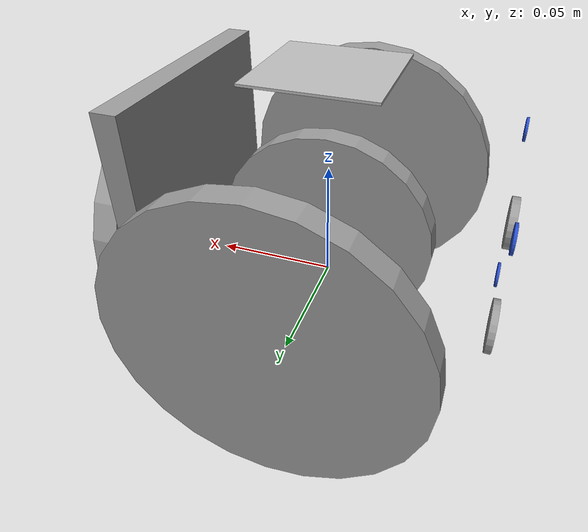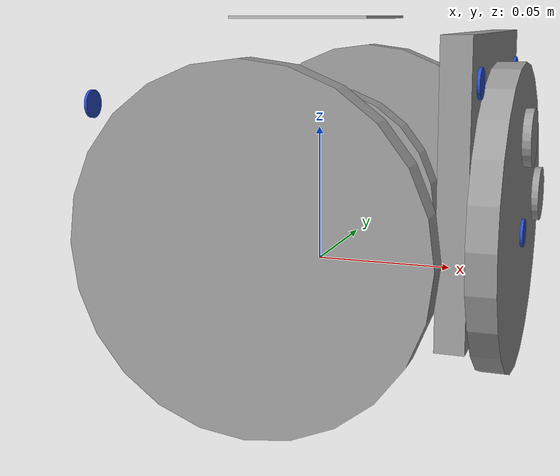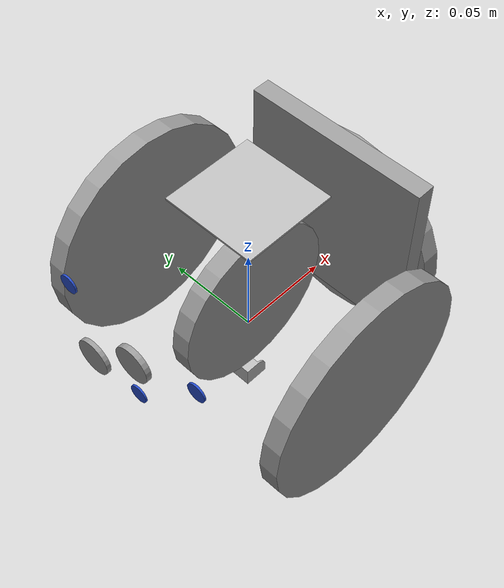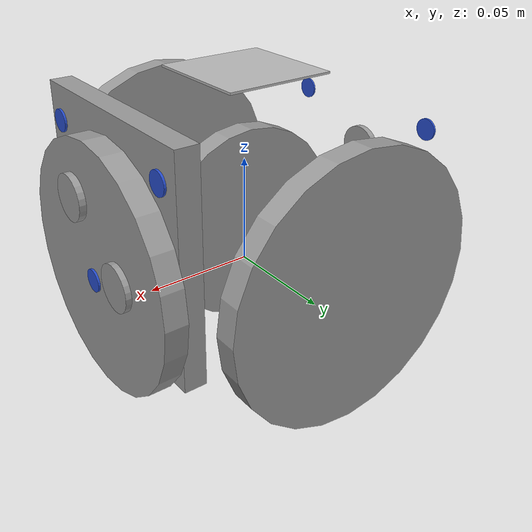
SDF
<?xml version='1.0'?>
<sdf version='1.6'>
  <model name='ditto1'>
    <link name='body'>
      <inertial>
        <mass>5</mass>
        <inertia>
          <ixx>0.166667</ixx>
          <ixy>0</ixy>
          <ixz>0</ixz>
          <iyy>0.166667</iyy>
          <iyz>0</iyz>
          <izz>0.166667</izz>
        </inertia>
        <pose frame=''>0 0 0 0 -0 0</pose>
      </inertial>
      <pose frame=''>0 -0 -0.036667 0 0 -1.5707</pose>
      <gravity>1</gravity>
      <self_collide>0</self_collide>
      <kinematic>0</kinematic>
      <enable_wind>0</enable_wind>
      <visual name='visual'>
        <pose frame=''>0 0 0 0 -0 0</pose>
        <geometry>
          <mesh>
            <uri>model://meshes/bodyCorrected.obj</uri>
            <scale>0.001 0.001 0.001</scale>
          </mesh>
        </geometry>
        <material>
          <shader type='pixel'>
            <normal_map>__default__</normal_map>
          </shader>
          <emissive>0 0 0 1</emissive>
        </material>
        <transparency>0</transparency>
        <cast_shadows>1</cast_shadows>
      </visual>
      <collision name='collision'>
        <laser_retro>0</laser_retro>
        <max_contacts>10</max_contacts>
        <pose frame=''>0 0 0 0 -0 0</pose>
        <geometry>
          <mesh>
            <uri>model://meshes/bodyCorrected.obj</uri>
            <scale>0.001 0.001 0.001</scale>
          </mesh>
        </geometry>
        <surface>
          <friction>
            <ode>
              <mu>1</mu>
              <mu2>1</mu2>
              <fdir1>0 0 0</fdir1>
              <slip1>0</slip1>
              <slip2>0</slip2>
            </ode>
            <torsional>
              <coefficient>1</coefficient>
              <patch_radius>0</patch_radius>
              <surface_radius>0</surface_radius>
              <use_patch_radius>1</use_patch_radius>
              <ode>
                <slip>0</slip>
              </ode>
            </torsional>
          </friction>
          <bounce>
            <restitution_coefficient>0</restitution_coefficient>
            <threshold>1e+06</threshold>
          </bounce>
          <contact>
            <collide_without_contact>0</collide_without_contact>
            <collide_without_contact_bitmask>1</collide_without_contact_bitmask>
            <collide_bitmask>1</collide_bitmask>
            <ode>
              <soft_cfm>0</soft_cfm>
              <soft_erp>0.2</soft_erp>
              <kp>1e+13</kp>
              <kd>1</kd>
              <max_vel>0.01</max_vel>
              <min_depth>0</min_depth>
            </ode>
            <bullet>
              <split_impulse>1</split_impulse>
              <split_impulse_penetration_threshold>-0.01</split_impulse_penetration_threshold>
              <soft_cfm>0</soft_cfm>
              <soft_erp>0.2</soft_erp>
              <kp>1e+13</kp>
              <kd>1</kd>
            </bullet>
          </contact>
        </surface>
      </collision>
    </link>
    <link name='april1'>
      <pose frame=''>0 0 0.09 0 -0 0</pose>
      <inertial>
        <pose frame=''>0 0 0 0 -0 0</pose>
        <mass>0.01</mass>
        <inertia>
          <ixx>0</ixx>
          <ixy>0</ixy>
          <ixz>0</ixz>
          <iyy>0</iyy>
          <iyz>0</iyz>
          <izz>0</izz>
        </inertia>
      </inertial>
      <self_collide>0</self_collide>
      <enable_wind>0</enable_wind>
      <kinematic>0</kinematic>
      <visual name='body_fixed_joint_lump__visual_visual'>
        <pose frame=''>0 0 0 0 -0 0</pose>
        <geometry>
          <mesh>
            <scale>1 1 1</scale>
            <uri>model://id1/meshes/id1.dae</uri>
          </mesh>
        </geometry>
        <material>
          <shader type='pixel'/>
        </material>
        <transparency>0</transparency>
        <cast_shadows>1</cast_shadows>
      </visual>
      <collision name='body_fixed_joint_lump__collision_collision'>
        <laser_retro>0</laser_retro>
        <max_contacts>10</max_contacts>
        <pose frame=''>0 0 0 0 -0 0</pose>
        <geometry>
          <mesh>
            <uri>model://id1/meshes/id1.dae</uri>
            <scale>1 1 1</scale>
          </mesh>
        </geometry>
        <surface>
          <friction>
            <ode>
              <mu>1</mu>
              <mu2>1</mu2>
              <fdir1>0 0 0</fdir1>
              <slip1>0</slip1>
              <slip2>0</slip2>
            </ode>
            <torsional>
              <coefficient>1</coefficient>
              <patch_radius>0</patch_radius>
              <surface_radius>0</surface_radius>
              <use_patch_radius>1</use_patch_radius>
              <ode>
                <slip>0</slip>
              </ode>
            </torsional>
          </friction>
          <bounce>
            <restitution_coefficient>0</restitution_coefficient>
            <threshold>1e+06</threshold>
          </bounce>
          <contact>
            <collide_without_contact>0</collide_without_contact>
            <collide_without_contact_bitmask>1</collide_without_contact_bitmask>
            <collide_bitmask>1</collide_bitmask>
            <ode>
              <soft_cfm>0</soft_cfm>
              <soft_erp>0.2</soft_erp>
              <kp>1e+13</kp>
              <kd>1</kd>
              <max_vel>0.01</max_vel>
              <min_depth>0</min_depth>
            </ode>
            <bullet>
              <split_impulse>1</split_impulse>
              <split_impulse_penetration_threshold>-0.01</split_impulse_penetration_threshold>
              <soft_cfm>0</soft_cfm>
              <soft_erp>0.2</soft_erp>
              <kp>1e+13</kp>
              <kd>1</kd>
            </bullet>
          </contact>
        </surface>
      </collision>
    </link>
    <link name='back_caster'>
      <inertial>
        <mass>0.09</mass>
        <inertia>
          <ixx>3.2e-06</ixx>
          <ixy>0</ixy>
          <ixz>0</ixz>
          <iyy>3.2e-06</iyy>
          <iyz>0</iyz>
          <izz>3.2e-06</izz>
        </inertia>
        <pose frame=''>0 0 0.036667 0 -0 0</pose>
      </inertial>
      <pose frame=''>-0.0545 -0 -0.025 0 -0 0</pose>
      <gravity>1</gravity>
      <self_collide>0</self_collide>
      <kinematic>0</kinematic>
      <enable_wind>0</enable_wind>
      <visual name='visual'>
        <pose frame=''>0 0 0 0 -0 0</pose>
        <geometry>
          <sphere>
            <radius>0.015</radius>
          </sphere>
        </geometry>
        <material>
          <lighting>1</lighting>
          <script>
            <uri>file://media/materials/scripts/gazebo.material</uri>
            <name>Gazebo/Red</name>
          </script>
          <shader type='pixel'>
            <normal_map>__default__</normal_map>
          </shader>
          <ambient>0.8 0 0 1</ambient>
          <diffuse>0.7 0.7 0.7 1</diffuse>
          <specular>0.01 0.01 0.01 1</specular>
          <emissive>0 0 0 1</emissive>
        </material>
        <transparency>1</transparency>
        <cast_shadows>1</cast_shadows>
      </visual>
      <collision name='collision'>
        <laser_retro>0</laser_retro>
        <max_contacts>10</max_contacts>
        <pose frame=''>0 0 0 0 -0 0</pose>
        <geometry>
          <sphere>
            <radius>0.015</radius>
          </sphere>
        </geometry>
        <surface>
          <friction>
            <ode>
              <mu>0</mu>
              <mu2>0</mu2>
              <fdir1>0 0 0</fdir1>
              <slip1>1</slip1>
              <slip2>1</slip2>
            </ode>
            <torsional>
              <coefficient>1</coefficient>
              <patch_radius>0</patch_radius>
              <surface_radius>0</surface_radius>
              <use_patch_radius>1</use_patch_radius>
              <ode>
                <slip>1</slip>
              </ode>
            </torsional>
          </friction>
          <bounce>
            <restitution_coefficient>0</restitution_coefficient>
            <threshold>1e+06</threshold>
          </bounce>
          <contact>
            <collide_without_contact>0</collide_without_contact>
            <collide_without_contact_bitmask>1</collide_without_contact_bitmask>
            <collide_bitmask>1</collide_bitmask>
            <ode>
              <soft_cfm>0</soft_cfm>
              <soft_erp>0.2</soft_erp>
              <kp>1e+13</kp>
              <kd>1</kd>
              <max_vel>0.01</max_vel>
              <min_depth>0</min_depth>
            </ode>
            <bullet>
              <split_impulse>1</split_impulse>
              <split_impulse_penetration_threshold>-0.01</split_impulse_penetration_threshold>
              <soft_cfm>0</soft_cfm>
              <soft_erp>0.2</soft_erp>
              <kp>1e+13</kp>
              <kd>1</kd>
            </bullet>
          </contact>
        </surface>
      </collision>
    </link>
    <link name='body_ir_sensor'>
      <inertial>
        <mass>1e-07</mass>
        <inertia>
          <ixx>0</ixx>
          <ixy>0</ixy>
          <ixz>0</ixz>
          <iyy>0</iyy>
          <iyz>0</iyz>
          <izz>0</izz>
        </inertia>
        <pose frame=''>0 0 0 0 -0 0</pose>
      </inertial>
      <pose frame=''>-0.071 -0 0.015 1.57068 -2e-06 -1.5707</pose>
      <gravity>1</gravity>
      <self_collide>0</self_collide>
      <kinematic>0</kinematic>
      <enable_wind>0</enable_wind>
      <sensor name='TeraRanger' type='ray'>
        <pose frame=''>0 0 0 0 -1.5707 0</pose>
        <visualize>0</visualize>
        <update_rate>5</update_rate>
        <ray>
          <scan>
            <horizontal>
              <samples>1</samples>
              <resolution>1</resolution>
              <min_angle>-0.01</min_angle>
              <max_angle>0.01</max_angle>
            </horizontal>
            <vertical>
              <samples>1</samples>
              <resolution>1</resolution>
              <min_angle>-0.01</min_angle>
              <max_angle>0.01</max_angle>
            </vertical>
          </scan>
          <range>
            <min>0.01</min>
            <max>2</max>
            <resolution>0.01</resolution>
          </range>
        </ray>
        <plugin name='gazebo_ros_range' filename='libgazebo_ros_range.so'>
          <gaussianNoise>0.005</gaussianNoise>
          <alwaysOn>1</alwaysOn>
          <updateRate>5</updateRate>
          <topicName>ditto1/body_ir</topicName>
          <frameName>body_ir_sensor</frameName>
          <fov>0.5</fov>
          <radiation>ultrasound</radiation>
          <robotNamespace>/</robotNamespace>
        </plugin>
      </sensor>
      <visual name='visual'>
        <pose frame=''>0 0 0 0 -0 0</pose>
        <geometry>
          <cylinder>
            <radius>0.005</radius>
            <length>0.001</length>
          </cylinder>
        </geometry>
        <material>
          <lighting>1</lighting>
          <script>
            <uri>file://media/materials/scripts/gazebo.material</uri>
            <name>Gazebo/Blue</name>
          </script>
          <shader type='pixel'>
            <normal_map>__default__</normal_map>
          </shader>
          <ambient>0.3 0.3 0.3 1</ambient>
          <diffuse>0.7 0.7 0.7 1</diffuse>
          <specular>0.01 0.01 0.01 1</specular>
          <emissive>0 0 0 1</emissive>
        </material>
        <transparency>0</transparency>
        <cast_shadows>1</cast_shadows>
      </visual>
      <collision name='box_collision'>
        <laser_retro>0</laser_retro>
        <max_contacts>10</max_contacts>
        <pose frame=''>0 0 0 0 -0 0</pose>
        <geometry>
          <cylinder>
            <radius>0.005</radius>
            <length>0.001</length>
          </cylinder>
        </geometry>
        <surface>
          <friction>
            <ode>
              <mu>1</mu>
              <mu2>1</mu2>
              <fdir1>0 0 0</fdir1>
              <slip1>0</slip1>
              <slip2>0</slip2>
            </ode>
            <torsional>
              <coefficient>1</coefficient>
              <patch_radius>0</patch_radius>
              <surface_radius>0</surface_radius>
              <use_patch_radius>1</use_patch_radius>
              <ode>
                <slip>0</slip>
              </ode>
            </torsional>
          </friction>
          <bounce>
            <restitution_coefficient>0</restitution_coefficient>
            <threshold>1e+06</threshold>
          </bounce>
          <contact>
            <collide_without_contact>0</collide_without_contact>
            <collide_without_contact_bitmask>1</collide_without_contact_bitmask>
            <collide_bitmask>1</collide_bitmask>
            <ode>
              <soft_cfm>0</soft_cfm>
              <soft_erp>0.2</soft_erp>
              <kp>1e+13</kp>
              <kd>1</kd>
              <max_vel>0.01</max_vel>
              <min_depth>0</min_depth>
            </ode>
            <bullet>
              <split_impulse>1</split_impulse>
              <split_impulse_penetration_threshold>-0.01</split_impulse_penetration_threshold>
              <soft_cfm>0</soft_cfm>
              <soft_erp>0.2</soft_erp>
              <kp>1e+13</kp>
              <kd>1</kd>
            </bullet>
          </contact>
        </surface>
      </collision>
    </link>
    <link name='body_magnet_north'>
      <inertial>
        <mass>1e-07</mass>
        <inertia>
          <ixx>0</ixx>
          <ixy>0</ixy>
          <ixz>0</ixz>
          <iyy>0</iyy>
          <iyz>0</iyz>
          <izz>0</izz>
        </inertia>
        <pose frame=''>0 0 0 0 -0 0</pose>
      </inertial>
      <pose frame=''>-0.0715 0.03 0.015 1.5707 -3e-05 -1.5707</pose>
      <gravity>1</gravity>
      <self_collide>0</self_collide>
      <kinematic>0</kinematic>
      <enable_wind>0</enable_wind>
      <sensor name='my_plugin_2' type='contact'>
        <plugin name='ContactPlugin_2' filename='libcontact.so'>
          <robotNamespace>/</robotNamespace>
          <magnetic_face>body_magnet_south</magnetic_face>
        </plugin>
        <contact>
          <collision>box_collision</collision>
          <topic>__default_topic__</topic>
        </contact>
        <update_rate>5</update_rate>
      </sensor>
      <visual name='visual'>
        <pose frame=''>0 0 0 0 -0 0</pose>
        <geometry>
          <cylinder>
            <radius>0.01</radius>
            <length>0.0025</length>
          </cylinder>
        </geometry>
        <material>
          <lighting>1</lighting>
          <script>
            <uri>file://media/materials/scripts/gazebo.material</uri>
            <name>Gazebo/Grey</name>
          </script>
          <shader type='pixel'>
            <normal_map>__default__</normal_map>
          </shader>
          <ambient>0.3 0.3 0.3 1</ambient>
          <diffuse>0.7 0.7 0.7 1</diffuse>
          <specular>0.01 0.01 0.01 1</specular>
          <emissive>0 0 0 1</emissive>
        </material>
        <transparency>0</transparency>
        <cast_shadows>1</cast_shadows>
      </visual>
      <collision name='box_collision'>
        <laser_retro>0</laser_retro>
        <max_contacts>10</max_contacts>
        <pose frame=''>0 0 0 0 -0 0</pose>
        <geometry>
          <cylinder>
            <radius>0.01</radius>
            <length>0.0025</length>
          </cylinder>
        </geometry>
        <surface>
          <friction>
            <ode>
              <mu>1</mu>
              <mu2>1</mu2>
              <fdir1>0 0 0</fdir1>
              <slip1>0</slip1>
              <slip2>0</slip2>
            </ode>
            <torsional>
              <coefficient>1</coefficient>
              <patch_radius>0</patch_radius>
              <surface_radius>0</surface_radius>
              <use_patch_radius>1</use_patch_radius>
              <ode>
                <slip>0</slip>
              </ode>
            </torsional>
          </friction>
          <bounce>
            <restitution_coefficient>0</restitution_coefficient>
            <threshold>1e+06</threshold>
          </bounce>
          <contact>
            <collide_without_contact>0</collide_without_contact>
            <collide_without_contact_bitmask>1</collide_without_contact_bitmask>
            <collide_bitmask>1</collide_bitmask>
            <ode>
              <soft_cfm>0</soft_cfm>
              <soft_erp>0.2</soft_erp>
              <kp>1e+13</kp>
              <kd>1</kd>
              <max_vel>0.01</max_vel>
              <min_depth>0</min_depth>
            </ode>
            <bullet>
              <split_impulse>1</split_impulse>
              <split_impulse_penetration_threshold>-0.01</split_impulse_penetration_threshold>
              <soft_cfm>0</soft_cfm>
              <soft_erp>0.2</soft_erp>
              <kp>1e+13</kp>
              <kd>1</kd>
            </bullet>
          </contact>
        </surface>
      </collision>
    </link>
    <link name='body_magnet_south'>
      <inertial>
        <mass>1e-07</mass>
        <inertia>
          <ixx>0</ixx>
          <ixy>0</ixy>
          <ixz>0</ixz>
          <iyy>0</iyy>
          <iyz>0</iyz>
          <izz>0</izz>
        </inertia>
        <pose frame=''>0 0 0 0 -0 0</pose>
      </inertial>
      <pose frame=''>-0.0715 0 0.04 1.5707 -4.3e-05 -1.5707</pose>
      <gravity>1</gravity>
      <self_collide>0</self_collide>
      <kinematic>0</kinematic>
      <enable_wind>0</enable_wind>
      <sensor name='my_plugin_2' type='contact'>
        <plugin name='ContactPlugin_2' filename='libcontact.so'>
          <robotNamespace>/</robotNamespace>
          <magnetic_face>body_magnet_north</magnetic_face>
        </plugin>
        <contact>
          <collision>box_collision</collision>
          <topic>__default_topic__</topic>
        </contact>
        <update_rate>5</update_rate>
      </sensor>
      <visual name='visual'>
        <pose frame=''>0 0 0 0 -0 0</pose>
        <geometry>
          <cylinder>
            <radius>0.01</radius>
            <length>0.003</length>
          </cylinder>
        </geometry>
        <material>
          <lighting>1</lighting>
          <script>
            <uri>file://media/materials/scripts/gazebo.material</uri>
            <name>Gazebo/Grey</name>
          </script>
          <shader type='pixel'>
            <normal_map>__default__</normal_map>
          </shader>
          <ambient>0.3 0.3 0.3 1</ambient>
          <diffuse>0.7 0.7 0.7 1</diffuse>
          <specular>0.01 0.01 0.01 1</specular>
          <emissive>0 0 0 1</emissive>
        </material>
        <transparency>0</transparency>
        <cast_shadows>1</cast_shadows>
      </visual>
      <collision name='box_collision'>
        <laser_retro>0</laser_retro>
        <max_contacts>10</max_contacts>
        <pose frame=''>0 0 0 0 -0 0</pose>
        <geometry>
          <cylinder>
            <radius>0.01</radius>
            <length>0.003</length>
          </cylinder>
        </geometry>
        <surface>
          <friction>
            <ode>
              <mu>1</mu>
              <mu2>1</mu2>
              <fdir1>0 0 0</fdir1>
              <slip1>0</slip1>
              <slip2>0</slip2>
            </ode>
            <torsional>
              <coefficient>1</coefficient>
              <patch_radius>0</patch_radius>
              <surface_radius>0</surface_radius>
              <use_patch_radius>1</use_patch_radius>
              <ode>
                <slip>0</slip>
              </ode>
            </torsional>
          </friction>
          <bounce>
            <restitution_coefficient>0</restitution_coefficient>
            <threshold>1e+06</threshold>
          </bounce>
          <contact>
            <collide_without_contact>0</collide_without_contact>
            <collide_without_contact_bitmask>1</collide_without_contact_bitmask>
            <collide_bitmask>1</collide_bitmask>
            <ode>
              <soft_cfm>0</soft_cfm>
              <soft_erp>0.2</soft_erp>
              <kp>1e+13</kp>
              <kd>1</kd>
              <max_vel>0.01</max_vel>
              <min_depth>0</min_depth>
            </ode>
            <bullet>
              <split_impulse>1</split_impulse>
              <split_impulse_penetration_threshold>-0.01</split_impulse_penetration_threshold>
              <soft_cfm>0</soft_cfm>
              <soft_erp>0.2</soft_erp>
              <kp>1e+13</kp>
              <kd>1</kd>
            </bullet>
          </contact>
        </surface>
      </collision>
    </link>
    <link name='body_tof1_sensor'>
      <inertial>
        <mass>1e-07</mass>
        <inertia>
          <ixx>0</ixx>
          <ixy>0</ixy>
          <ixz>0</ixz>
          <iyy>0</iyy>
          <iyz>0</iyz>
          <izz>0</izz>
        </inertia>
        <pose frame=''>0 0 0 0 -0 0</pose>
      </inertial>
      <pose frame=''>-0.071 0.04 0.06 1.5707 -5e-05 -1.5707</pose>
      <gravity>1</gravity>
      <self_collide>0</self_collide>
      <kinematic>0</kinematic>
      <enable_wind>0</enable_wind>
      <sensor name='TeraRanger' type='ray'>
        <pose frame=''>0 0 0 0 -1.5707 0</pose>
        <visualize>0</visualize>
        <update_rate>5</update_rate>
        <ray>
          <scan>
            <horizontal>
              <samples>3</samples>
              <resolution>1</resolution>
              <min_angle>-0.03</min_angle>
              <max_angle>0.03</max_angle>
            </horizontal>
            <vertical>
              <samples>3</samples>
              <resolution>1</resolution>
              <min_angle>-0.25</min_angle>
              <max_angle>0.25</max_angle>
            </vertical>
          </scan>
          <range>
            <min>0.01</min>
            <max>2</max>
            <resolution>0.01</resolution>
          </range>
        </ray>
        <plugin name='gazebo_ros_range' filename='libgazebo_ros_range.so'>
          <gaussianNoise>0.005</gaussianNoise>
          <alwaysOn>1</alwaysOn>
          <updateRate>5</updateRate>
          <topicName>ditto1/body_tof1</topicName>
          <frameName>body_tof1_sensor</frameName>
          <fov>0.5</fov>
          <radiation>ultrasound</radiation>
          <robotNamespace>/</robotNamespace>
        </plugin>
      </sensor>
      <visual name='visual'>
        <pose frame=''>0 0 0 0 -0 0</pose>
        <geometry>
          <cylinder>
            <radius>0.005</radius>
            <length>0.001</length>
          </cylinder>
        </geometry>
        <material>
          <lighting>1</lighting>
          <script>
            <uri>file://media/materials/scripts/gazebo.material</uri>
            <name>Gazebo/Blue</name>
          </script>
          <shader type='pixel'>
            <normal_map>__default__</normal_map>
          </shader>
          <ambient>0.3 0.3 0.3 1</ambient>
          <diffuse>0.7 0.7 0.7 1</diffuse>
          <specular>0.01 0.01 0.01 1</specular>
          <emissive>0 0 0 1</emissive>
        </material>
        <transparency>0</transparency>
        <cast_shadows>1</cast_shadows>
      </visual>
      <collision name='box_collision'>
        <laser_retro>0</laser_retro>
        <max_contacts>10</max_contacts>
        <pose frame=''>0 0 0 0 -0 0</pose>
        <geometry>
          <cylinder>
            <radius>0.005</radius>
            <length>0.001</length>
          </cylinder>
        </geometry>
        <surface>
          <friction>
            <ode>
              <mu>1</mu>
              <mu2>1</mu2>
              <fdir1>0 0 0</fdir1>
              <slip1>0</slip1>
              <slip2>0</slip2>
            </ode>
            <torsional>
              <coefficient>1</coefficient>
              <patch_radius>0</patch_radius>
              <surface_radius>0</surface_radius>
              <use_patch_radius>1</use_patch_radius>
              <ode>
                <slip>0</slip>
              </ode>
            </torsional>
          </friction>
          <bounce>
            <restitution_coefficient>0</restitution_coefficient>
            <threshold>1e+06</threshold>
          </bounce>
          <contact>
            <collide_without_contact>0</collide_without_contact>
            <collide_without_contact_bitmask>1</collide_without_contact_bitmask>
            <collide_bitmask>1</collide_bitmask>
            <ode>
              <soft_cfm>0</soft_cfm>
              <soft_erp>0.2</soft_erp>
              <kp>1e+13</kp>
              <kd>1</kd>
              <max_vel>0.01</max_vel>
              <min_depth>0</min_depth>
            </ode>
            <bullet>
              <split_impulse>1</split_impulse>
              <split_impulse_penetration_threshold>-0.01</split_impulse_penetration_threshold>
              <soft_cfm>0</soft_cfm>
              <soft_erp>0.2</soft_erp>
              <kp>1e+13</kp>
              <kd>1</kd>
            </bullet>
          </contact>
        </surface>
      </collision>
    </link>
    <link name='body_tof2_sensor'>
      <inertial>
        <mass>1e-07</mass>
        <inertia>
          <ixx>0</ixx>
          <ixy>0</ixy>
          <ixz>0</ixz>
          <iyy>0</iyy>
          <iyz>0</iyz>
          <izz>0</izz>
        </inertia>
        <pose frame=''>0 0 0 0 -0 0</pose>
      </inertial>
      <pose frame=''>-0.071 -0.04 0.06 1.5707 -0 -1.5707</pose>
      <gravity>1</gravity>
      <self_collide>0</self_collide>
      <kinematic>0</kinematic>
      <enable_wind>0</enable_wind>
      <sensor name='TeraRanger' type='ray'>
        <pose frame=''>0 0 0 0 -1.5707 0</pose>
        <visualize>0</visualize>
        <update_rate>5</update_rate>
        <ray>
          <scan>
            <horizontal>
              <samples>3</samples>
              <resolution>1</resolution>
              <min_angle>-0.03</min_angle>
              <max_angle>0.03</max_angle>
            </horizontal>
            <vertical>
              <samples>3</samples>
              <resolution>1</resolution>
              <min_angle>-0.25</min_angle>
              <max_angle>0.25</max_angle>
            </vertical>
          </scan>
          <range>
            <min>0.01</min>
            <max>2</max>
            <resolution>0.01</resolution>
          </range>
        </ray>
        <plugin name='gazebo_ros_range' filename='libgazebo_ros_range.so'>
          <gaussianNoise>0.005</gaussianNoise>
          <alwaysOn>1</alwaysOn>
          <updateRate>5</updateRate>
          <topicName>ditto1/body_tof2</topicName>
          <frameName>body_tof2_sensor</frameName>
          <fov>0.5</fov>
          <radiation>ultrasound</radiation>
          <robotNamespace>/</robotNamespace>
        </plugin>
      </sensor>
      <visual name='visual'>
        <pose frame=''>0 0 0 0 -0 0</pose>
        <geometry>
          <cylinder>
            <radius>0.005</radius>
            <length>0.001</length>
          </cylinder>
        </geometry>
        <material>
          <lighting>1</lighting>
          <script>
            <uri>file://media/materials/scripts/gazebo.material</uri>
            <name>Gazebo/Blue</name>
          </script>
          <shader type='pixel'>
            <normal_map>__default__</normal_map>
          </shader>
          <ambient>0.3 0.3 0.3 1</ambient>
          <diffuse>0.7 0.7 0.7 1</diffuse>
          <specular>0.01 0.01 0.01 1</specular>
          <emissive>0 0 0 1</emissive>
        </material>
        <transparency>0</transparency>
        <cast_shadows>1</cast_shadows>
      </visual>
      <collision name='box_collision'>
        <laser_retro>0</laser_retro>
        <max_contacts>10</max_contacts>
        <pose frame=''>0 0 0 0 -0 0</pose>
        <geometry>
          <cylinder>
            <radius>0.005</radius>
            <length>0.001</length>
          </cylinder>
        </geometry>
        <surface>
          <friction>
            <ode>
              <mu>1</mu>
              <mu2>1</mu2>
              <fdir1>0 0 0</fdir1>
              <slip1>0</slip1>
              <slip2>0</slip2>
            </ode>
            <torsional>
              <coefficient>1</coefficient>
              <patch_radius>0</patch_radius>
              <surface_radius>0</surface_radius>
              <use_patch_radius>1</use_patch_radius>
              <ode>
                <slip>0</slip>
              </ode>
            </torsional>
          </friction>
          <bounce>
            <restitution_coefficient>0</restitution_coefficient>
            <threshold>1e+06</threshold>
          </bounce>
          <contact>
            <collide_without_contact>0</collide_without_contact>
            <collide_without_contact_bitmask>1</collide_without_contact_bitmask>
            <collide_bitmask>1</collide_bitmask>
            <ode>
              <soft_cfm>0</soft_cfm>
              <soft_erp>0.2</soft_erp>
              <kp>1e+13</kp>
              <kd>1</kd>
              <max_vel>0.01</max_vel>
              <min_depth>0</min_depth>
            </ode>
            <bullet>
              <split_impulse>1</split_impulse>
              <split_impulse_penetration_threshold>-0.01</split_impulse_penetration_threshold>
              <soft_cfm>0</soft_cfm>
              <soft_erp>0.2</soft_erp>
              <kp>1e+13</kp>
              <kd>1</kd>
            </bullet>
          </contact>
        </surface>
      </collision>
    </link>
    <link name='face_pan'>
      <inertial>
        <mass>0.1</mass>
        <inertia>
          <ixx>0.145833</ixx>
          <ixy>0</ixy>
          <ixz>0</ixz>
          <iyy>0.145833</iyy>
          <iyz>0</iyz>
          <izz>0.125</izz>
        </inertia>
        <pose frame=''>0 0 0 0 -0 0</pose>
      </inertial>
      <pose frame=''>0.06 0 0.035 -3.13999 -0 -1.5707</pose>
      <gravity>1</gravity>
      <self_collide>0</self_collide>
      <kinematic>0</kinematic>
      <enable_wind>0</enable_wind>
      <visual name='visual'>
        <pose frame=''>0 0 0 0 -0 0</pose>
        <geometry>
          <box>
            <size>0.1 0.01 0.1</size>
          </box>
        </geometry>
        <material>
          <lighting>1</lighting>
          <script>
            <uri>file://media/materials/scripts/gazebo.material</uri>
            <name>Gazebo/Grey</name>
          </script>
          <shader type='pixel'>
            <normal_map>__default__</normal_map>
          </shader>
          <ambient>0.3 0.3 0.3 1</ambient>
          <diffuse>0.7 0.7 0.7 1</diffuse>
          <specular>0.01 0.01 0.01 1</specular>
          <emissive>0 0 0 1</emissive>
        </material>
        <transparency>0</transparency>
        <cast_shadows>1</cast_shadows>
      </visual>
      <collision name='collision'>
        <laser_retro>0</laser_retro>
        <max_contacts>10</max_contacts>
        <pose frame=''>0 0 0 0 -0 0</pose>
        <geometry>
          <box>
            <size>0.1 0.01 0.1</size>
          </box>
        </geometry>
        <surface>
          <friction>
            <ode>
              <mu>1</mu>
              <mu2>1</mu2>
              <fdir1>0 0 0</fdir1>
              <slip1>0</slip1>
              <slip2>0</slip2>
            </ode>
            <torsional>
              <coefficient>1</coefficient>
              <patch_radius>0</patch_radius>
              <surface_radius>0</surface_radius>
              <use_patch_radius>1</use_patch_radius>
              <ode>
                <slip>0</slip>
              </ode>
            </torsional>
          </friction>
          <bounce>
            <restitution_coefficient>0</restitution_coefficient>
            <threshold>1e+06</threshold>
          </bounce>
          <contact>
            <collide_without_contact>0</collide_without_contact>
            <collide_without_contact_bitmask>1</collide_without_contact_bitmask>
            <collide_bitmask>1</collide_bitmask>
            <ode>
              <soft_cfm>0</soft_cfm>
              <soft_erp>0.2</soft_erp>
              <kp>1e+13</kp>
              <kd>1</kd>
              <max_vel>0.01</max_vel>
              <min_depth>0</min_depth>
            </ode>
            <bullet>
              <split_impulse>1</split_impulse>
              <split_impulse_penetration_threshold>-0.01</split_impulse_penetration_threshold>
              <soft_cfm>0</soft_cfm>
              <soft_erp>0.2</soft_erp>
              <kp>1e+13</kp>
              <kd>1</kd>
            </bullet>
          </contact>
        </surface>
      </collision>
    </link>
    <link name='face_tilt'>
      <inertial>
        <mass>0.0001</mass>
        <inertia>
          <ixx>0.145833</ixx>
          <ixy>0</ixy>
          <ixz>0</ixz>
          <iyy>0.145833</iyy>
          <iyz>0</iyz>
          <izz>0.125</izz>
        </inertia>
        <pose frame=''>0 0 0 0 -0 0</pose>
      </inertial>
      <pose frame=''>0 -0 0.02 -1.57054 1.56989 -3.14143</pose>
      <gravity>1</gravity>
      <self_collide>0</self_collide>
      <kinematic>0</kinematic>
      <enable_wind>0</enable_wind>
      <visual name='visual'>
        <pose frame=''>0 0 0 0 -0 0</pose>
        <geometry>
          <cylinder>
            <radius>0.045</radius>
            <length>0.01</length>
          </cylinder>
        </geometry>
        <material>
          <lighting>1</lighting>
          <script>
            <uri>file://media/materials/scripts/gazebo.material</uri>
            <name>Gazebo/Grey</name>
          </script>
          <shader type='pixel'>
            <normal_map>__default__</normal_map>
          </shader>
          <ambient>0.3 0.3 0.3 1</ambient>
          <diffuse>0.7 0.7 0.7 1</diffuse>
          <specular>0.01 0.01 0.01 1</specular>
          <emissive>0 0 0 1</emissive>
        </material>
        <transparency>0</transparency>
        <cast_shadows>1</cast_shadows>
      </visual>
      <collision name='collision'>
        <laser_retro>0</laser_retro>
        <max_contacts>10</max_contacts>
        <pose frame=''>0 0 0 0 -0 0</pose>
        <geometry>
          <cylinder>
            <radius>0.045</radius>
            <length>0.01</length>
          </cylinder>
        </geometry>
        <surface>
          <friction>
            <ode>
              <mu>1</mu>
              <mu2>1</mu2>
              <fdir1>0 0 0</fdir1>
              <slip1>0</slip1>
              <slip2>0</slip2>
            </ode>
            <torsional>
              <coefficient>1</coefficient>
              <patch_radius>0</patch_radius>
              <surface_radius>0</surface_radius>
              <use_patch_radius>1</use_patch_radius>
              <ode>
                <slip>0</slip>
              </ode>
            </torsional>
          </friction>
          <bounce>
            <restitution_coefficient>0</restitution_coefficient>
            <threshold>1e+06</threshold>
          </bounce>
          <contact>
            <collide_without_contact>0</collide_without_contact>
            <collide_without_contact_bitmask>1</collide_without_contact_bitmask>
            <collide_bitmask>1</collide_bitmask>
            <ode>
              <soft_cfm>0</soft_cfm>
              <soft_erp>0.2</soft_erp>
              <kp>1e+13</kp>
              <kd>1</kd>
              <max_vel>0.01</max_vel>
              <min_depth>0</min_depth>
            </ode>
            <bullet>
              <split_impulse>1</split_impulse>
              <split_impulse_penetration_threshold>-0.01</split_impulse_penetration_threshold>
              <soft_cfm>0</soft_cfm>
              <soft_erp>0.2</soft_erp>
              <kp>1e+13</kp>
              <kd>1</kd>
            </bullet>
          </contact>
        </surface>
      </collision>
    </link>
    <link name='front_caster'>
      <inertial>
        <mass>0.09</mass>
        <inertia>
          <ixx>3.2e-06</ixx>
          <ixy>0</ixy>
          <ixz>0</ixz>
          <iyy>3.2e-06</iyy>
          <iyz>0</iyz>
          <izz>3.2e-06</izz>
        </inertia>
        <pose frame=''>0 0 0 0 -0 0</pose>
      </inertial>
      <pose frame=''>0.045 0 -0.025 0 -0 0</pose>
      <gravity>1</gravity>
      <self_collide>0</self_collide>
      <kinematic>0</kinematic>
      <enable_wind>0</enable_wind>
      <visual name='visual'>
        <pose frame=''>0 0 0 0 -0 0</pose>
        <geometry>
          <sphere>
            <radius>0.015</radius>
          </sphere>
        </geometry>
        <material>
          <lighting>1</lighting>
          <script>
            <uri>file://media/materials/scripts/gazebo.material</uri>
            <name>Gazebo/Red</name>
          </script>
          <shader type='pixel'>
            <normal_map>__default__</normal_map>
          </shader>
          <ambient>0.8 0 0 1</ambient>
          <diffuse>0.8 0 0 1</diffuse>
          <specular>0.8 0 0 1</specular>
          <emissive>0.8 0 0 1</emissive>
        </material>
        <transparency>1</transparency>
        <cast_shadows>1</cast_shadows>
      </visual>
      <collision name='collision'>
        <laser_retro>0</laser_retro>
        <max_contacts>10</max_contacts>
        <pose frame=''>0 0 0 0 -0 0</pose>
        <geometry>
          <sphere>
            <radius>0.015</radius>
          </sphere>
        </geometry>
        <surface>
          <friction>
            <ode>
              <mu>0</mu>
              <mu2>0</mu2>
              <fdir1>0 0 0</fdir1>
              <slip1>1</slip1>
              <slip2>1</slip2>
            </ode>
            <torsional>
              <coefficient>1</coefficient>
              <patch_radius>0</patch_radius>
              <surface_radius>0</surface_radius>
              <use_patch_radius>1</use_patch_radius>
              <ode>
                <slip>1</slip>
              </ode>
            </torsional>
          </friction>
          <bounce>
            <restitution_coefficient>0</restitution_coefficient>
            <threshold>1e+06</threshold>
          </bounce>
          <contact>
            <collide_without_contact>0</collide_without_contact>
            <collide_without_contact_bitmask>1</collide_without_contact_bitmask>
            <collide_bitmask>1</collide_bitmask>
            <ode>
              <soft_cfm>0</soft_cfm>
              <soft_erp>0.2</soft_erp>
              <kp>1e+13</kp>
              <kd>1</kd>
              <max_vel>0.01</max_vel>
              <min_depth>0</min_depth>
            </ode>
            <bullet>
              <split_impulse>1</split_impulse>
              <split_impulse_penetration_threshold>-0.01</split_impulse_penetration_threshold>
              <soft_cfm>0</soft_cfm>
              <soft_erp>0.2</soft_erp>
              <kp>1e+13</kp>
              <kd>1</kd>
            </bullet>
          </contact>
        </surface>
      </collision>
    </link>
    <link name='front_face'>
      <inertial>
        <mass>0.5</mass>
        <inertia>
          <ixx>0.166667</ixx>
          <ixy>0</ixy>
          <ixz>0</ixz>
          <iyy>0.166667</iyy>
          <iyz>0</iyz>
          <izz>0.166667</izz>
        </inertia>
        <pose frame=''>0 0 0 0 -0 0</pose>
      </inertial>
      <pose frame=''>0.07 -0 0.02 -1.9e-05 -2e-06 -1.5707</pose>
      <gravity>1</gravity>
      <self_collide>0</self_collide>
      <kinematic>0</kinematic>
      <enable_wind>0</enable_wind>
      <visual name='visual'>
        <pose frame=''>0 0 0 1.5707 -0 0</pose>
        <geometry>
          <cylinder>
            <radius>0.055</radius>
            <length>0.01</length>
          </cylinder>
        </geometry>
        <material>
          <lighting>1</lighting>
          <script>
            <uri>file://media/materials/scripts/gazebo.material</uri>
            <name>Gazebo/Grey</name>
          </script>
          <shader type='pixel'>
            <normal_map>__default__</normal_map>
          </shader>
          <ambient>0.3 0.3 0.3 1</ambient>
          <diffuse>0.7 0.7 0.7 1</diffuse>
          <specular>0.01 0.01 0.01 1</specular>
          <emissive>0 0 0 1</emissive>
        </material>
        <transparency>0</transparency>
        <cast_shadows>1</cast_shadows>
      </visual>
      <collision name='collision'>
        <laser_retro>0</laser_retro>
        <max_contacts>10</max_contacts>
        <pose frame=''>0 0 0 1.5707 -0 0</pose>
        <geometry>
          <cylinder>
            <radius>0.05</radius>
            <length>0.01</length>
          </cylinder>
        </geometry>
        <surface>
          <friction>
            <ode>
              <mu>1</mu>
              <mu2>1</mu2>
              <fdir1>0 0 0</fdir1>
              <slip1>0</slip1>
              <slip2>0</slip2>
            </ode>
            <torsional>
              <coefficient>1</coefficient>
              <patch_radius>0</patch_radius>
              <surface_radius>0</surface_radius>
              <use_patch_radius>1</use_patch_radius>
              <ode>
                <slip>0</slip>
              </ode>
            </torsional>
          </friction>
          <bounce>
            <restitution_coefficient>0</restitution_coefficient>
            <threshold>1e+06</threshold>
          </bounce>
          <contact>
            <collide_without_contact>0</collide_without_contact>
            <collide_without_contact_bitmask>1</collide_without_contact_bitmask>
            <collide_bitmask>1</collide_bitmask>
            <ode>
              <soft_cfm>0</soft_cfm>
              <soft_erp>0.2</soft_erp>
              <kp>1e+13</kp>
              <kd>1</kd>
              <max_vel>0.01</max_vel>
              <min_depth>0</min_depth>
            </ode>
            <bullet>
              <split_impulse>1</split_impulse>
              <split_impulse_penetration_threshold>-0.01</split_impulse_penetration_threshold>
              <soft_cfm>0</soft_cfm>
              <soft_erp>0.2</soft_erp>
              <kp>1e+13</kp>
              <kd>1</kd>
            </bullet>
          </contact>
        </surface>
      </collision>
    </link>
    <link name='front_face_ir_sensor'>
      <inertial>
        <mass>1e-07</mass>
        <inertia>
          <ixx>0</ixx>
          <ixy>0</ixy>
          <ixz>0</ixz>
          <iyy>0</iyy>
          <iyz>0</iyz>
          <izz>0</izz>
        </inertia>
        <pose frame=''>0 0 0 0 -0 0</pose>
      </inertial>
      <pose frame=''>0.076 0 0.015 1.5707 -0 -1.5707</pose>
      <gravity>1</gravity>
      <self_collide>0</self_collide>
      <kinematic>0</kinematic>
      <enable_wind>0</enable_wind>
      <sensor name='TeraRanger' type='ray'>
        <pose frame=''>0 0 0 0 1.5707 0</pose>
        <visualize>0</visualize>
        <update_rate>5</update_rate>
        <ray>
          <scan>
            <horizontal>
              <samples>1</samples>
              <resolution>1</resolution>
              <min_angle>-0.03</min_angle>
              <max_angle>0.03</max_angle>
            </horizontal>
            <vertical>
              <samples>1</samples>
              <resolution>1</resolution>
              <min_angle>-0.25</min_angle>
              <max_angle>0.25</max_angle>
            </vertical>
          </scan>
          <range>
            <min>0.01</min>
            <max>2</max>
            <resolution>0.01</resolution>
          </range>
        </ray>
        <plugin name='gazebo_ros_range' filename='libgazebo_ros_range.so'>
          <gaussianNoise>0.005</gaussianNoise>
          <alwaysOn>1</alwaysOn>
          <updateRate>5</updateRate>
          <topicName>ditto1/front_face_ir</topicName>
          <frameName>front_face_ir_sensor</frameName>
          <fov>0.5</fov>
          <radiation>ultrasound</radiation>
          <robotNamespace>/</robotNamespace>
        </plugin>
      </sensor>
      <visual name='visual'>
        <pose frame=''>0 0 0 0 -0 0</pose>
        <geometry>
          <cylinder>
            <radius>0.005</radius>
            <length>0.001</length>
          </cylinder>
        </geometry>
        <material>
          <lighting>1</lighting>
          <script>
            <uri>file://media/materials/scripts/gazebo.material</uri>
            <name>Gazebo/Blue</name>
          </script>
          <shader type='pixel'>
            <normal_map>__default__</normal_map>
          </shader>
          <ambient>0.3 0.3 0.3 1</ambient>
          <diffuse>0.7 0.7 0.7 1</diffuse>
          <specular>0.01 0.01 0.01 1</specular>
          <emissive>1 1 1 1</emissive>
        </material>
        <transparency>0</transparency>
        <cast_shadows>1</cast_shadows>
      </visual>
      <collision name='box_collision'>
        <laser_retro>0</laser_retro>
        <max_contacts>10</max_contacts>
        <pose frame=''>0 0 0 0 -0 0</pose>
        <geometry>
          <cylinder>
            <radius>0.005</radius>
            <length>0.001</length>
          </cylinder>
        </geometry>
        <surface>
          <friction>
            <ode>
              <mu>1</mu>
              <mu2>1</mu2>
              <fdir1>0 0 0</fdir1>
              <slip1>0</slip1>
              <slip2>0</slip2>
            </ode>
            <torsional>
              <coefficient>1</coefficient>
              <patch_radius>0</patch_radius>
              <surface_radius>0</surface_radius>
              <use_patch_radius>1</use_patch_radius>
              <ode>
                <slip>0</slip>
              </ode>
            </torsional>
          </friction>
          <bounce>
            <restitution_coefficient>0</restitution_coefficient>
            <threshold>1e+06</threshold>
          </bounce>
          <contact>
            <collide_without_contact>0</collide_without_contact>
            <collide_without_contact_bitmask>1</collide_without_contact_bitmask>
            <collide_bitmask>1</collide_bitmask>
            <ode>
              <soft_cfm>0</soft_cfm>
              <soft_erp>0.2</soft_erp>
              <kp>1e+13</kp>
              <kd>1</kd>
              <max_vel>0.01</max_vel>
              <min_depth>0</min_depth>
            </ode>
            <bullet>
              <split_impulse>1</split_impulse>
              <split_impulse_penetration_threshold>-0.01</split_impulse_penetration_threshold>
              <soft_cfm>0</soft_cfm>
              <soft_erp>0.2</soft_erp>
              <kp>1e+13</kp>
              <kd>1</kd>
            </bullet>
          </contact>
        </surface>
      </collision>
    </link>
    <link name='front_face_magnet_north'>
      <inertial>
        <mass>1e-07</mass>
        <inertia>
          <ixx>0</ixx>
          <ixy>0</ixy>
          <ixz>0</ixz>
          <iyy>0</iyy>
          <iyz>0</iyz>
          <izz>0</izz>
        </inertia>
        <pose frame=''>0 0 0 0 -0 0</pose>
      </inertial>
      <pose frame=''>0.078 0.03 0.015 1.5707 -1.3e-05 -1.5707</pose>
      <gravity>1</gravity>
      <self_collide>0</self_collide>
      <kinematic>0</kinematic>
      <enable_wind>0</enable_wind>
      <sensor name='my_plugin_1' type='contact'>
        <plugin name='ContactPlugin_1' filename='libcontact.so'>
          <robotNamespace>/</robotNamespace>
          <magnetic_face>front_face_magnet_north</magnetic_face>
        </plugin>
        <contact>
          <collision>box_collision</collision>
          <topic>__default_topic__</topic>
        </contact>
        <update_rate>5</update_rate>
      </sensor>
      <visual name='visual'>
        <pose frame=''>0.005 0.01 0 0 -0 0</pose>
        <geometry>
          <cylinder>
            <radius>0.01</radius>
            <length>0.0025</length>
          </cylinder>
        </geometry>
        <material>
          <lighting>1</lighting>
          <script>
            <uri>file://media/materials/scripts/gazebo.material</uri>
            <name>Gazebo/Grey</name>
          </script>
          <shader type='pixel'>
            <normal_map>__default__</normal_map>
          </shader>
          <ambient>0.3 0.3 0.3 1</ambient>
          <diffuse>0.7 0.7 0.7 1</diffuse>
          <specular>0.01 0.01 0.01 1</specular>
          <emissive>0 0 0 1</emissive>
        </material>
        <transparency>0</transparency>
        <cast_shadows>1</cast_shadows>
      </visual>
      <collision name='box_collision'>
        <laser_retro>0</laser_retro>
        <max_contacts>10</max_contacts>
        <pose frame=''>0 0 0 0 -0 0</pose>
        <geometry>
          <cylinder>
            <radius>0.01</radius>
            <length>0.0025</length>
          </cylinder>
        </geometry>
        <surface>
          <friction>
            <ode>
              <mu>1</mu>
              <mu2>1</mu2>
              <fdir1>0 0 0</fdir1>
              <slip1>0</slip1>
              <slip2>0</slip2>
            </ode>
            <torsional>
              <coefficient>1</coefficient>
              <patch_radius>0</patch_radius>
              <surface_radius>0</surface_radius>
              <use_patch_radius>1</use_patch_radius>
              <ode>
                <slip>0</slip>
              </ode>
            </torsional>
          </friction>
          <bounce>
            <restitution_coefficient>0</restitution_coefficient>
            <threshold>1e+06</threshold>
          </bounce>
          <contact>
            <collide_without_contact>0</collide_without_contact>
            <collide_without_contact_bitmask>1</collide_without_contact_bitmask>
            <collide_bitmask>1</collide_bitmask>
            <ode>
              <soft_cfm>0</soft_cfm>
              <soft_erp>0.2</soft_erp>
              <kp>1e+13</kp>
              <kd>1</kd>
              <max_vel>0.01</max_vel>
              <min_depth>0</min_depth>
            </ode>
            <bullet>
              <split_impulse>1</split_impulse>
              <split_impulse_penetration_threshold>-0.01</split_impulse_penetration_threshold>
              <soft_cfm>0</soft_cfm>
              <soft_erp>0.2</soft_erp>
              <kp>1e+13</kp>
              <kd>1</kd>
            </bullet>
          </contact>
        </surface>
      </collision>
    </link>
    <link name='front_face_magnet_south'>
      <inertial>
        <mass>1e-07</mass>
        <inertia>
          <ixx>0</ixx>
          <ixy>0</ixy>
          <ixz>0</ixz>
          <iyy>0</iyy>
          <iyz>0</iyz>
          <izz>0</izz>
        </inertia>
        <pose frame=''>0 0 0 0 -0 0</pose>
      </inertial>
      <pose frame=''>0.078 -0.003 0.04 1.5707 -2.4e-05 -1.5707</pose>
      <gravity>1</gravity>
      <self_collide>0</self_collide>
      <kinematic>0</kinematic>
      <enable_wind>0</enable_wind>
      <sensor name='my_plugin_1' type='contact'>
        <plugin name='ContactPlugin_1' filename='libcontact.so'>
          <robotNamespace>/</robotNamespace>
          <magnetic_face>front_face_magnet_south</magnetic_face>
        </plugin>
        <contact>
          <collision>box_collision</collision>
          <topic>__default_topic__</topic>
        </contact>
        <update_rate>5</update_rate>
      </sensor>
      <visual name='visual'>
        <pose frame=''>0.005 0.01 0 0 -0 0</pose>
        <geometry>
          <cylinder>
            <radius>0.01</radius>
            <length>0.003</length>
          </cylinder>
        </geometry>
        <material>
          <lighting>1</lighting>
          <script>
            <uri>file://media/materials/scripts/gazebo.material</uri>
            <name>Gazebo/Grey</name>
          </script>
          <shader type='pixel'>
            <normal_map>__default__</normal_map>
          </shader>
          <ambient>0.3 0.3 0.3 1</ambient>
          <diffuse>0.7 0.7 0.7 1</diffuse>
          <specular>0.01 0.01 0.01 1</specular>
          <emissive>0 0 0 1</emissive>
        </material>
        <transparency>0</transparency>
        <cast_shadows>1</cast_shadows>
      </visual>
      <collision name='box_collision'>
        <laser_retro>0</laser_retro>
        <max_contacts>10</max_contacts>
        <pose frame=''>0 0 0 0 -0 0</pose>
        <geometry>
          <cylinder>
            <radius>0.01</radius>
            <length>0.003</length>
          </cylinder>
        </geometry>
        <surface>
          <friction>
            <ode>
              <mu>1</mu>
              <mu2>1</mu2>
              <fdir1>0 0 0</fdir1>
              <slip1>0</slip1>
              <slip2>0</slip2>
            </ode>
            <torsional>
              <coefficient>1</coefficient>
              <patch_radius>0</patch_radius>
              <surface_radius>0</surface_radius>
              <use_patch_radius>1</use_patch_radius>
              <ode>
                <slip>0</slip>
              </ode>
            </torsional>
          </friction>
          <bounce>
            <restitution_coefficient>0</restitution_coefficient>
            <threshold>1e+06</threshold>
          </bounce>
          <contact>
            <collide_without_contact>0</collide_without_contact>
            <collide_without_contact_bitmask>1</collide_without_contact_bitmask>
            <collide_bitmask>1</collide_bitmask>
            <ode>
              <soft_cfm>0</soft_cfm>
              <soft_erp>0.2</soft_erp>
              <kp>1e+13</kp>
              <kd>1</kd>
              <max_vel>0.01</max_vel>
              <min_depth>0</min_depth>
            </ode>
            <bullet>
              <split_impulse>1</split_impulse>
              <split_impulse_penetration_threshold>-0.01</split_impulse_penetration_threshold>
              <soft_cfm>0</soft_cfm>
              <soft_erp>0.2</soft_erp>
              <kp>1e+13</kp>
              <kd>1</kd>
            </bullet>
          </contact>
        </surface>
      </collision>
    </link>
    <link name='front_face_tof1_sensor'>
      <inertial>
        <mass>1e-07</mass>
        <inertia>
          <ixx>0</ixx>
          <ixy>0</ixy>
          <ixz>0</ixz>
          <iyy>0</iyy>
          <iyz>0</iyz>
          <izz>0</izz>
        </inertia>
        <pose frame=''>0 0 0 0 -0 0</pose>
      </inertial>
      <pose frame=''>0.066 0.04 0.07 1.5707 -0 -1.5707</pose>
      <gravity>1</gravity>
      <self_collide>0</self_collide>
      <kinematic>0</kinematic>
      <enable_wind>0</enable_wind>
      <sensor name='TeraRanger' type='ray'>
        <pose frame=''>0 0 0 0 1.5707 0</pose>
        <visualize>0</visualize>
        <update_rate>5</update_rate>
        <ray>
          <scan>
            <horizontal>
              <samples>3</samples>
              <resolution>1</resolution>
              <min_angle>-0.03</min_angle>
              <max_angle>0.03</max_angle>
            </horizontal>
            <vertical>
              <samples>3</samples>
              <resolution>1</resolution>
              <min_angle>-0.25</min_angle>
              <max_angle>0.25</max_angle>
            </vertical>
          </scan>
          <range>
            <min>0.01</min>
            <max>2</max>
            <resolution>0.01</resolution>
          </range>
        </ray>
        <plugin name='gazebo_ros_range' filename='libgazebo_ros_range.so'>
          <gaussianNoise>0.005</gaussianNoise>
          <alwaysOn>1</alwaysOn>
          <updateRate>5</updateRate>
          <topicName>ditto1/front_face_tof1</topicName>
          <frameName>front_face_tof1_sensor</frameName>
          <fov>0.5</fov>
          <radiation>ultrasound</radiation>
          <robotNamespace>/</robotNamespace>
        </plugin>
      </sensor>
      <visual name='visual'>
        <pose frame=''>0 0 0 0 -0 0</pose>
        <geometry>
          <cylinder>
            <radius>0.005</radius>
            <length>0.001</length>
          </cylinder>
        </geometry>
        <material>
          <lighting>1</lighting>
          <script>
            <uri>file://media/materials/scripts/gazebo.material</uri>
            <name>Gazebo/Blue</name>
          </script>
          <shader type='pixel'>
            <normal_map>__default__</normal_map>
          </shader>
          <ambient>0.3 0.3 0.3 1</ambient>
          <diffuse>0.7 0.7 0.7 1</diffuse>
          <specular>0.01 0.01 0.01 1</specular>
          <emissive>1 1 1 1</emissive>
        </material>
        <transparency>0</transparency>
        <cast_shadows>1</cast_shadows>
      </visual>
      <collision name='box_collision'>
        <laser_retro>0</laser_retro>
        <max_contacts>10</max_contacts>
        <pose frame=''>0 0 0 0 -0 0</pose>
        <geometry>
          <cylinder>
            <radius>0.005</radius>
            <length>0.001</length>
          </cylinder>
        </geometry>
        <surface>
          <friction>
            <ode>
              <mu>1</mu>
              <mu2>1</mu2>
              <fdir1>0 0 0</fdir1>
              <slip1>0</slip1>
              <slip2>0</slip2>
            </ode>
            <torsional>
              <coefficient>1</coefficient>
              <patch_radius>0</patch_radius>
              <surface_radius>0</surface_radius>
              <use_patch_radius>1</use_patch_radius>
              <ode>
                <slip>0</slip>
              </ode>
            </torsional>
          </friction>
          <bounce>
            <restitution_coefficient>0</restitution_coefficient>
            <threshold>1e+06</threshold>
          </bounce>
          <contact>
            <collide_without_contact>0</collide_without_contact>
            <collide_without_contact_bitmask>1</collide_without_contact_bitmask>
            <collide_bitmask>1</collide_bitmask>
            <ode>
              <soft_cfm>0</soft_cfm>
              <soft_erp>0.2</soft_erp>
              <kp>1e+13</kp>
              <kd>1</kd>
              <max_vel>0.01</max_vel>
              <min_depth>0</min_depth>
            </ode>
            <bullet>
              <split_impulse>1</split_impulse>
              <split_impulse_penetration_threshold>-0.01</split_impulse_penetration_threshold>
              <soft_cfm>0</soft_cfm>
              <soft_erp>0.2</soft_erp>
              <kp>1e+13</kp>
              <kd>1</kd>
            </bullet>
          </contact>
        </surface>
      </collision>
    </link>
    <link name='front_face_tof2_sensor'>
      <inertial>
        <mass>1e-07</mass>
        <inertia>
          <ixx>0</ixx>
          <ixy>0</ixy>
          <ixz>0</ixz>
          <iyy>0</iyy>
          <iyz>0</iyz>
          <izz>0</izz>
        </inertia>
        <pose frame=''>0 0 0 0 -0 0</pose>
      </inertial>
      <pose frame=''>0.066 -0.04 0.07 1.5707 -0 -1.5707</pose>
      <gravity>1</gravity>
      <self_collide>0</self_collide>
      <kinematic>0</kinematic>
      <enable_wind>0</enable_wind>
      <sensor name='TeraRanger' type='ray'>
        <pose frame=''>0 0 0 0 1.5707 0</pose>
        <visualize>0</visualize>
        <update_rate>5</update_rate>
        <ray>
          <scan>
            <horizontal>
              <samples>3</samples>
              <resolution>1</resolution>
              <min_angle>-0.03</min_angle>
              <max_angle>0.03</max_angle>
            </horizontal>
            <vertical>
              <samples>3</samples>
              <resolution>1</resolution>
              <min_angle>-0.25</min_angle>
              <max_angle>0.25</max_angle>
            </vertical>
          </scan>
          <range>
            <min>0.01</min>
            <max>2</max>
            <resolution>0.01</resolution>
          </range>
        </ray>
        <plugin name='gazebo_ros_range' filename='libgazebo_ros_range.so'>
          <gaussianNoise>0.005</gaussianNoise>
          <alwaysOn>1</alwaysOn>
          <updateRate>5</updateRate>
          <topicName>ditto1/front_face_tof2</topicName>
          <frameName>front_face_tof2_sensor</frameName>
          <fov>0.5</fov>
          <radiation>ultrasound</radiation>
          <robotNamespace>/</robotNamespace>
        </plugin>
      </sensor>
      <visual name='visual'>
        <pose frame=''>0 0 0 0 -0 0</pose>
        <geometry>
          <cylinder>
            <radius>0.005</radius>
            <length>0.001</length>
          </cylinder>
        </geometry>
        <material>
          <lighting>1</lighting>
          <script>
            <uri>file://media/materials/scripts/gazebo.material</uri>
            <name>Gazebo/Blue</name>
          </script>
          <shader type='pixel'>
            <normal_map>__default__</normal_map>
          </shader>
          <ambient>0.3 0.3 0.3 1</ambient>
          <diffuse>0.7 0.7 0.7 1</diffuse>
          <specular>0.01 0.01 0.01 1</specular>
          <emissive>1 1 1 1</emissive>
        </material>
        <transparency>0</transparency>
        <cast_shadows>1</cast_shadows>
      </visual>
      <collision name='box_collision'>
        <laser_retro>0</laser_retro>
        <max_contacts>10</max_contacts>
        <pose frame=''>0 0 0 0 -0 0</pose>
        <geometry>
          <cylinder>
            <radius>0.005</radius>
            <length>0.001</length>
          </cylinder>
        </geometry>
        <surface>
          <friction>
            <ode>
              <mu>1</mu>
              <mu2>1</mu2>
              <fdir1>0 0 0</fdir1>
              <slip1>0</slip1>
              <slip2>0</slip2>
            </ode>
            <torsional>
              <coefficient>1</coefficient>
              <patch_radius>0</patch_radius>
              <surface_radius>0</surface_radius>
              <use_patch_radius>1</use_patch_radius>
              <ode>
                <slip>0</slip>
              </ode>
            </torsional>
          </friction>
          <bounce>
            <restitution_coefficient>0</restitution_coefficient>
            <threshold>1e+06</threshold>
          </bounce>
          <contact>
            <collide_without_contact>0</collide_without_contact>
            <collide_without_contact_bitmask>1</collide_without_contact_bitmask>
            <collide_bitmask>1</collide_bitmask>
            <ode>
              <soft_cfm>0</soft_cfm>
              <soft_erp>0.2</soft_erp>
              <kp>1e+13</kp>
              <kd>1</kd>
              <max_vel>0.01</max_vel>
              <min_depth>0</min_depth>
            </ode>
            <bullet>
              <split_impulse>1</split_impulse>
              <split_impulse_penetration_threshold>-0.01</split_impulse_penetration_threshold>
              <soft_cfm>0</soft_cfm>
              <soft_erp>0.2</soft_erp>
              <kp>1e+13</kp>
              <kd>1</kd>
            </bullet>
          </contact>
        </surface>
      </collision>
    </link>
    <link name='left_wheel'>
      <inertial>
        <mass>0.5</mass>
        <inertia>
          <ixx>0.145833</ixx>
          <ixy>0</ixy>
          <ixz>0</ixz>
          <iyy>0.145833</iyy>
          <iyz>0</iyz>
          <izz>0.125</izz>
        </inertia>
        <pose frame=''>0 0 0 0 -0 0</pose>
      </inertial>
      <pose frame=''>0 0.07 0.018333 1.5707 -0 0</pose>
      <gravity>1</gravity>
      <self_collide>0</self_collide>
      <kinematic>0</kinematic>
      <enable_wind>0</enable_wind>
      <visual name='visual'>
        <pose frame=''>0 0 0 0 -0 0</pose>
        <geometry>
          <cylinder>
            <radius>0.06</radius>
            <length>0.01</length>
          </cylinder>
        </geometry>
        <material>
          <lighting>1</lighting>
          <script>
            <uri>file://media/materials/scripts/gazebo.material</uri>
            <name>Gazebo/Grey</name>
          </script>
          <shader type='pixel'>
            <normal_map>__default__</normal_map>
          </shader>
          <ambient>0.3 0.3 0.3 1</ambient>
          <diffuse>0.7 0.7 0.7 1</diffuse>
          <specular>0.01 0.01 0.01 1</specular>
          <emissive>0 0 0 1</emissive>
        </material>
        <transparency>0</transparency>
        <cast_shadows>1</cast_shadows>
      </visual>
      <collision name='collision'>
        <laser_retro>0</laser_retro>
        <max_contacts>10</max_contacts>
        <pose frame=''>0 0 0 0 -0 0</pose>
        <geometry>
          <cylinder>
            <radius>0.06</radius>
            <length>0.01</length>
          </cylinder>
        </geometry>
        <surface>
          <friction>
            <ode>
              <mu>1</mu>
              <mu2>1</mu2>
              <fdir1>0 0 0</fdir1>
              <slip1>0</slip1>
              <slip2>0</slip2>
            </ode>
            <torsional>
              <coefficient>1</coefficient>
              <patch_radius>0</patch_radius>
              <surface_radius>0</surface_radius>
              <use_patch_radius>1</use_patch_radius>
              <ode>
                <slip>0</slip>
              </ode>
            </torsional>
          </friction>
          <bounce>
            <restitution_coefficient>0</restitution_coefficient>
            <threshold>1e+06</threshold>
          </bounce>
          <contact>
            <collide_without_contact>0</collide_without_contact>
            <collide_without_contact_bitmask>1</collide_without_contact_bitmask>
            <collide_bitmask>1</collide_bitmask>
            <ode>
              <soft_cfm>0</soft_cfm>
              <soft_erp>0.2</soft_erp>
              <kp>1e+13</kp>
              <kd>1</kd>
              <max_vel>0.01</max_vel>
              <min_depth>0</min_depth>
            </ode>
            <bullet>
              <split_impulse>1</split_impulse>
              <split_impulse_penetration_threshold>-0.01</split_impulse_penetration_threshold>
              <soft_cfm>0</soft_cfm>
              <soft_erp>0.2</soft_erp>
              <kp>1e+13</kp>
              <kd>1</kd>
            </bullet>
          </contact>
        </surface>
      </collision>
    </link>
    <link name='right_wheel'>
      <inertial>
        <mass>0.5</mass>
        <inertia>
          <ixx>0.145833</ixx>
          <ixy>0</ixy>
          <ixz>0</ixz>
          <iyy>0.145833</iyy>
          <iyz>0</iyz>
          <izz>0.125</izz>
        </inertia>
        <pose frame=''>0 0 0 0 -0 0</pose>
      </inertial>
      <pose frame=''>0 -0.07 0.018333 1.5707 -0 0</pose>
      <gravity>1</gravity>
      <self_collide>0</self_collide>
      <kinematic>0</kinematic>
      <enable_wind>0</enable_wind>
      <visual name='visual'>
        <pose frame=''>0 0 0 0 -0 0</pose>
        <geometry>
          <cylinder>
            <radius>0.06</radius>
            <length>0.01</length>
          </cylinder>
        </geometry>
        <material>
          <lighting>1</lighting>
          <script>
            <uri>file://media/materials/scripts/gazebo.material</uri>
            <name>Gazebo/Grey</name>
          </script>
          <shader type='pixel'>
            <normal_map>__default__</normal_map>
          </shader>
          <ambient>0.3 0.3 0.3 1</ambient>
          <diffuse>0.7 0.7 0.7 1</diffuse>
          <specular>0.01 0.01 0.01 1</specular>
          <emissive>0 0 0 1</emissive>
        </material>
        <transparency>0</transparency>
        <cast_shadows>1</cast_shadows>
      </visual>
      <collision name='collision'>
        <laser_retro>0</laser_retro>
        <max_contacts>10</max_contacts>
        <pose frame=''>0 0 0 0 -0 0</pose>
        <geometry>
          <cylinder>
            <radius>0.06</radius>
            <length>0.01</length>
          </cylinder>
        </geometry>
        <surface>
          <friction>
            <ode>
              <mu>1</mu>
              <mu2>1</mu2>
              <fdir1>0 0 0</fdir1>
              <slip1>0</slip1>
              <slip2>0</slip2>
            </ode>
            <torsional>
              <coefficient>1</coefficient>
              <patch_radius>0</patch_radius>
              <surface_radius>0</surface_radius>
              <use_patch_radius>1</use_patch_radius>
              <ode>
                <slip>0</slip>
              </ode>
            </torsional>
          </friction>
          <bounce>
            <restitution_coefficient>0</restitution_coefficient>
            <threshold>1e+06</threshold>
          </bounce>
          <contact>
            <collide_without_contact>0</collide_without_contact>
            <collide_without_contact_bitmask>1</collide_without_contact_bitmask>
            <collide_bitmask>1</collide_bitmask>
            <ode>
              <soft_cfm>0</soft_cfm>
              <soft_erp>0.2</soft_erp>
              <kp>1e+13</kp>
              <kd>1</kd>
              <max_vel>0.01</max_vel>
              <min_depth>0</min_depth>
            </ode>
            <bullet>
              <split_impulse>1</split_impulse>
              <split_impulse_penetration_threshold>-0.01</split_impulse_penetration_threshold>
              <soft_cfm>0</soft_cfm>
              <soft_erp>0.2</soft_erp>
              <kp>1e+13</kp>
              <kd>1</kd>
            </bullet>
          </contact>
        </surface>
      </collision>
    </link>
    <joint name='back_caster_body' type='revolute'>
      <parent>body</parent>
      <child>back_caster</child>
      <pose frame=''>0 0 0 0 -0 0</pose>
      <axis>
        <xyz>1 0 0</xyz>
        <use_parent_model_frame>0</use_parent_model_frame>
        <limit>
          <lower>0</lower>
          <upper>0</upper>
          <effort>-1</effort>
          <velocity>-1</velocity>
        </limit>
        <dynamics>
          <spring_reference>0</spring_reference>
          <spring_stiffness>0</spring_stiffness>
          <damping>0</damping>
          <friction>0</friction>
        </dynamics>
      </axis>
      <physics>
        <ode>
          <limit>
            <cfm>0</cfm>
            <erp>0.2</erp>
          </limit>
          <suspension>
            <cfm>0</cfm>
            <erp>0.2</erp>
          </suspension>
        </ode>
      </physics>
    </joint>
    <joint name='body_JOINT_0' type='revolute'>
      <parent>body</parent>
      <child>body_magnet_south</child>
      <pose frame=''>0 0 0 0 -0 0</pose>
      <axis>
        <xyz>1 0 0</xyz>
        <use_parent_model_frame>0</use_parent_model_frame>
        <limit>
          <lower>0</lower>
          <upper>0</upper>
          <effort>-1</effort>
          <velocity>-1</velocity>
        </limit>
        <dynamics>
          <spring_reference>0</spring_reference>
          <spring_stiffness>0</spring_stiffness>
          <damping>0</damping>
          <friction>0</friction>
        </dynamics>
      </axis>
      <physics>
        <ode>
          <limit>
            <cfm>0</cfm>
            <erp>0.2</erp>
          </limit>
          <suspension>
            <cfm>0</cfm>
            <erp>0.2</erp>
          </suspension>
        </ode>
      </physics>
    </joint>
    <joint name='body_JOINT_1' type='revolute'>
      <parent>body</parent>
      <child>body_magnet_north</child>
      <pose frame=''>0 0 0 0 -0 0</pose>
      <axis>
        <xyz>1 0 0</xyz>
        <use_parent_model_frame>0</use_parent_model_frame>
        <limit>
          <lower>0</lower>
          <upper>0</upper>
          <effort>-1</effort>
          <velocity>-1</velocity>
        </limit>
        <dynamics>
          <spring_reference>0</spring_reference>
          <spring_stiffness>0</spring_stiffness>
          <damping>0</damping>
          <friction>0</friction>
        </dynamics>
      </axis>
      <physics>
        <ode>
          <limit>
            <cfm>0</cfm>
            <erp>0.2</erp>
          </limit>
          <suspension>
            <cfm>0</cfm>
            <erp>0.2</erp>
          </suspension>
        </ode>
      </physics>
    </joint>
    <joint name='body_ir_sensor_joint' type='revolute'>
      <parent>body</parent>
      <child>body_ir_sensor</child>
      <pose frame=''>0 0 0 0 -0 0</pose>
      <axis>
        <xyz>0 0 0</xyz>
        <use_parent_model_frame>0</use_parent_model_frame>
        <limit>
          <lower>0</lower>
          <upper>-0</upper>
          <effort>-1</effort>
          <velocity>-1</velocity>
        </limit>
        <dynamics>
          <spring_reference>0</spring_reference>
          <spring_stiffness>0</spring_stiffness>
          <damping>0</damping>
          <friction>0</friction>
        </dynamics>
      </axis>
      <physics>
        <ode>
          <limit>
            <cfm>0</cfm>
            <erp>0.2</erp>
          </limit>
          <suspension>
            <cfm>0</cfm>
            <erp>0.2</erp>
          </suspension>
        </ode>
      </physics>
    </joint>
    <joint name='body_tag1' type='fixed'>
      <parent>body</parent>
      <child>april1</child>
      <pose frame=''>0  0  0 0 0 0</pose>
      <axis>
        <xyz>0 0 0</xyz>
        <use_parent_model_frame>0</use_parent_model_frame>
      </axis>
    </joint>
    <joint name='body_tof1_joint' type='revolute'>
      <parent>body</parent>
      <child>body_tof1_sensor</child>
      <pose frame=''>0 0 0 0 -0 0</pose>
      <axis>
        <xyz>1 0 0</xyz>
        <use_parent_model_frame>0</use_parent_model_frame>
        <limit>
          <lower>0</lower>
          <upper>0</upper>
          <effort>-1</effort>
          <velocity>-1</velocity>
        </limit>
        <dynamics>
          <spring_reference>0</spring_reference>
          <spring_stiffness>0</spring_stiffness>
          <damping>0</damping>
          <friction>0</friction>
        </dynamics>
      </axis>
      <physics>
        <ode>
          <limit>
            <cfm>0</cfm>
            <erp>0.2</erp>
          </limit>
          <suspension>
            <cfm>0</cfm>
            <erp>0.2</erp>
          </suspension>
        </ode>
      </physics>
    </joint>
    <joint name='body_tof2_joint' type='revolute'>
      <parent>body</parent>
      <child>body_tof2_sensor</child>
      <pose frame=''>0 0 0 0 -0 0</pose>
      <axis>
        <xyz>1 0 0</xyz>
        <use_parent_model_frame>0</use_parent_model_frame>
        <limit>
          <lower>0</lower>
          <upper>0</upper>
          <effort>-1</effort>
          <velocity>-1</velocity>
        </limit>
        <dynamics>
          <spring_reference>0</spring_reference>
          <spring_stiffness>0</spring_stiffness>
          <damping>0</damping>
          <friction>0</friction>
        </dynamics>
      </axis>
      <physics>
        <ode>
          <limit>
            <cfm>0</cfm>
            <erp>0.2</erp>
          </limit>
          <suspension>
            <cfm>0</cfm>
            <erp>0.2</erp>
          </suspension>
        </ode>
      </physics>
    </joint>
    <joint name='fixed_joint' type='revolute'>
      <parent>face_tilt</parent>
      <child>face_pan</child>
      <pose frame=''>0 0 0 0 -0 0</pose>
      <axis>
        <xyz>0 0 1</xyz>
        <use_parent_model_frame>0</use_parent_model_frame>
        <limit>
          <lower>0</lower>
          <upper>0</upper>
          <effort>-1</effort>
          <velocity>-1</velocity>
        </limit>
        <dynamics>
          <spring_reference>0</spring_reference>
          <spring_stiffness>0</spring_stiffness>
          <damping>0</damping>
          <friction>0</friction>
        </dynamics>
      </axis>
      <physics>
        <ode>
          <limit>
            <cfm>0</cfm>
            <erp>0.2</erp>
          </limit>
          <suspension>
            <cfm>0</cfm>
            <erp>0.2</erp>
          </suspension>
        </ode>
      </physics>
    </joint>
    <joint name='front_caster_body' type='revolute'>
      <parent>body</parent>
      <child>front_caster</child>
      <pose frame=''>0 0 0 0 -0 0</pose>
      <axis>
        <xyz>1 0 0</xyz>
        <use_parent_model_frame>0</use_parent_model_frame>
        <limit>
          <lower>0</lower>
          <upper>0</upper>
          <effort>-1</effort>
          <velocity>-1</velocity>
        </limit>
        <dynamics>
          <spring_reference>0</spring_reference>
          <spring_stiffness>0</spring_stiffness>
          <damping>0</damping>
          <friction>0</friction>
        </dynamics>
      </axis>
      <physics>
        <ode>
          <limit>
            <cfm>0</cfm>
            <erp>0.2</erp>
          </limit>
          <suspension>
            <cfm>0</cfm>
            <erp>0.2</erp>
          </suspension>
        </ode>
      </physics>
    </joint>
    <joint name='front_face_JOINT_0' type='revolute'>
      <parent>front_face</parent>
      <child>front_face_magnet_north</child>
      <pose frame=''>0 0 0 0 -0 0</pose>
      <axis>
        <xyz>1 0 0</xyz>
        <use_parent_model_frame>0</use_parent_model_frame>
        <limit>
          <lower>0</lower>
          <upper>0</upper>
          <effort>-1</effort>
          <velocity>-1</velocity>
        </limit>
        <dynamics>
          <spring_reference>0</spring_reference>
          <spring_stiffness>0</spring_stiffness>
          <damping>0</damping>
          <friction>0</friction>
        </dynamics>
      </axis>
      <physics>
        <ode>
          <limit>
            <cfm>0</cfm>
            <erp>0.2</erp>
          </limit>
          <suspension>
            <cfm>0</cfm>
            <erp>0.2</erp>
          </suspension>
        </ode>
      </physics>
    </joint>
    <joint name='front_face_JOINT_1' type='revolute'>
      <parent>front_face</parent>
      <child>front_face_magnet_south</child>
      <pose frame=''>0 0 0 0 -0 0</pose>
      <axis>
        <xyz>1 0 0</xyz>
        <use_parent_model_frame>0</use_parent_model_frame>
        <limit>
          <lower>0</lower>
          <upper>0</upper>
          <effort>-1</effort>
          <velocity>-1</velocity>
        </limit>
        <dynamics>
          <spring_reference>0</spring_reference>
          <spring_stiffness>0</spring_stiffness>
          <damping>0</damping>
          <friction>0</friction>
        </dynamics>
      </axis>
      <physics>
        <ode>
          <limit>
            <cfm>0</cfm>
            <erp>0.2</erp>
          </limit>
          <suspension>
            <cfm>0</cfm>
            <erp>0.2</erp>
          </suspension>
        </ode>
      </physics>
    </joint>
    <joint name='front_face_ir_joint' type='revolute'>
      <parent>front_face</parent>
      <child>front_face_ir_sensor</child>
      <pose frame=''>0 0 0 0 -0 0</pose>
      <axis>
        <xyz>0 0 0</xyz>
        <use_parent_model_frame>0</use_parent_model_frame>
        <limit>
          <lower>0</lower>
          <upper>0</upper>
          <effort>-1</effort>
          <velocity>-1</velocity>
        </limit>
        <dynamics>
          <spring_reference>0</spring_reference>
          <spring_stiffness>0</spring_stiffness>
          <damping>0</damping>
          <friction>0</friction>
        </dynamics>
      </axis>
      <physics>
        <ode>
          <limit>
            <cfm>0</cfm>
            <erp>0.2</erp>
          </limit>
          <suspension>
            <cfm>0</cfm>
            <erp>0.2</erp>
          </suspension>
        </ode>
      </physics>
    </joint>
    <joint name='front_face_tof1_joint' type='revolute'>
      <parent>face_pan</parent>
      <child>front_face_tof1_sensor</child>
      <pose frame=''>0 0 0 0 -0 0</pose>
      <axis>
        <xyz>1 0 0</xyz>
        <use_parent_model_frame>0</use_parent_model_frame>
        <limit>
          <lower>0</lower>
          <upper>0</upper>
          <effort>-1</effort>
          <velocity>-1</velocity>
        </limit>
        <dynamics>
          <spring_reference>0</spring_reference>
          <spring_stiffness>0</spring_stiffness>
          <damping>0</damping>
          <friction>0</friction>
        </dynamics>
      </axis>
      <physics>
        <ode>
          <limit>
            <cfm>0</cfm>
            <erp>0.2</erp>
          </limit>
          <suspension>
            <cfm>0</cfm>
            <erp>0.2</erp>
          </suspension>
        </ode>
      </physics>
    </joint>
    <joint name='front_face_tof2_joint' type='revolute'>
      <parent>face_pan</parent>
      <child>front_face_tof2_sensor</child>
      <pose frame=''>0 0 0 0 -0 0</pose>
      <axis>
        <xyz>1 0 0</xyz>
        <use_parent_model_frame>0</use_parent_model_frame>
        <limit>
          <lower>-0</lower>
          <upper>0</upper>
          <effort>-1</effort>
          <velocity>-1</velocity>
        </limit>
        <dynamics>
          <spring_reference>0</spring_reference>
          <spring_stiffness>0</spring_stiffness>
          <damping>0</damping>
          <friction>0</friction>
        </dynamics>
      </axis>
      <physics>
        <ode>
          <limit>
            <cfm>0</cfm>
            <erp>0.2</erp>
          </limit>
          <suspension>
            <cfm>0</cfm>
            <erp>0.2</erp>
          </suspension>
        </ode>
      </physics>
    </joint>
    <joint name='left_wheel_joint' type='revolute'>
      <parent>body</parent>
      <child>left_wheel</child>
      <pose frame=''>0 0 0 0 -0 0</pose>
      <axis>
        <xyz>0 0 -1</xyz>
        <use_parent_model_frame>0</use_parent_model_frame>
        <limit>
          <lower>-1.79769e+308</lower>
          <upper>1.79769e+308</upper>
          <effort>-1</effort>
          <velocity>-1</velocity>
        </limit>
        <dynamics>
          <spring_reference>0</spring_reference>
          <spring_stiffness>0</spring_stiffness>
          <damping>0</damping>
          <friction>0</friction>
        </dynamics>
      </axis>
      <physics>
        <ode>
          <limit>
            <cfm>0</cfm>
            <erp>0.2</erp>
          </limit>
          <suspension>
            <cfm>0</cfm>
            <erp>0.2</erp>
          </suspension>
        </ode>
      </physics>
    </joint>
    <joint name='pan_joint' type='revolute'>
      <parent>face_pan</parent>
      <child>front_face</child>
      <pose frame=''>0 0 0 0 -0 0</pose>
      <axis>
        <xyz>0 1 0</xyz>
        <use_parent_model_frame>0</use_parent_model_frame>
        <limit>
          <lower>-1.79769e+308</lower>
          <upper>1.79769e+308</upper>
          <effort>-1</effort>
          <velocity>-1</velocity>
        </limit>
        <dynamics>
          <spring_reference>0</spring_reference>
          <spring_stiffness>0</spring_stiffness>
          <damping>0</damping>
          <friction>0</friction>
        </dynamics>
      </axis>
      <physics>
        <ode>
          <limit>
            <cfm>0</cfm>
            <erp>0.2</erp>
          </limit>
          <suspension>
            <cfm>0</cfm>
            <erp>0.2</erp>
          </suspension>
        </ode>
      </physics>
    </joint>
    <joint name='right_wheel_joint' type='revolute'>
      <parent>body</parent>
      <child>right_wheel</child>
      <pose frame=''>0 0 0 0 -0 0</pose>
      <axis>
        <xyz>0 0 -1</xyz>
        <use_parent_model_frame>0</use_parent_model_frame>
        <limit>
          <lower>-1.79769e+308</lower>
          <upper>1.79769e+308</upper>
          <effort>-1</effort>
          <velocity>-1</velocity>
        </limit>
        <dynamics>
          <spring_reference>0</spring_reference>
          <spring_stiffness>0</spring_stiffness>
          <damping>0</damping>
          <friction>0</friction>
        </dynamics>
      </axis>
      <physics>
        <ode>
          <limit>
            <cfm>0</cfm>
            <erp>0.2</erp>
          </limit>
          <suspension>
            <cfm>0</cfm>
            <erp>0.2</erp>
          </suspension>
        </ode>
      </physics>
    </joint>
    <joint name='tilt_joint' type='revolute'>
      <parent>body</parent>
      <child>face_tilt</child>
      <pose frame=''>0 0 0 0 -0 0</pose>
      <axis>
        <xyz>0 0 1</xyz>
        <use_parent_model_frame>0</use_parent_model_frame>
        <limit>
          <lower>0</lower>
          <upper>1.5707</upper>
          <effort>-1</effort>
          <velocity>-1</velocity>
        </limit>
        <dynamics>
          <spring_reference>0</spring_reference>
          <spring_stiffness>0</spring_stiffness>
          <damping>0</damping>
          <friction>0</friction>
        </dynamics>
      </axis>
      <physics>
        <ode>
          <limit>
            <cfm>0</cfm>
            <erp>0.2</erp>
          </limit>
          <suspension>
            <cfm>0</cfm>
            <erp>0.2</erp>
          </suspension>
        </ode>
      </physics>
    </joint>
    <static>0</static>
    <allow_auto_disable>1</allow_auto_disable>
    <plugin name='my_speed_controller_plugin' filename='libmy_speed_controller_plugin.so'>
      <namespace_model>GPabstractV2</namespace_model>
      <activate_pid_control>no</activate_pid_control>
      <wheel_kp>0.1</wheel_kp>
      <wheel_ki>0.0</wheel_ki>
      <wheel_kd>0.0</wheel_kd>
      <robotNamespace>/</robotNamespace>
    </plugin>
  </model>
</sdf>
